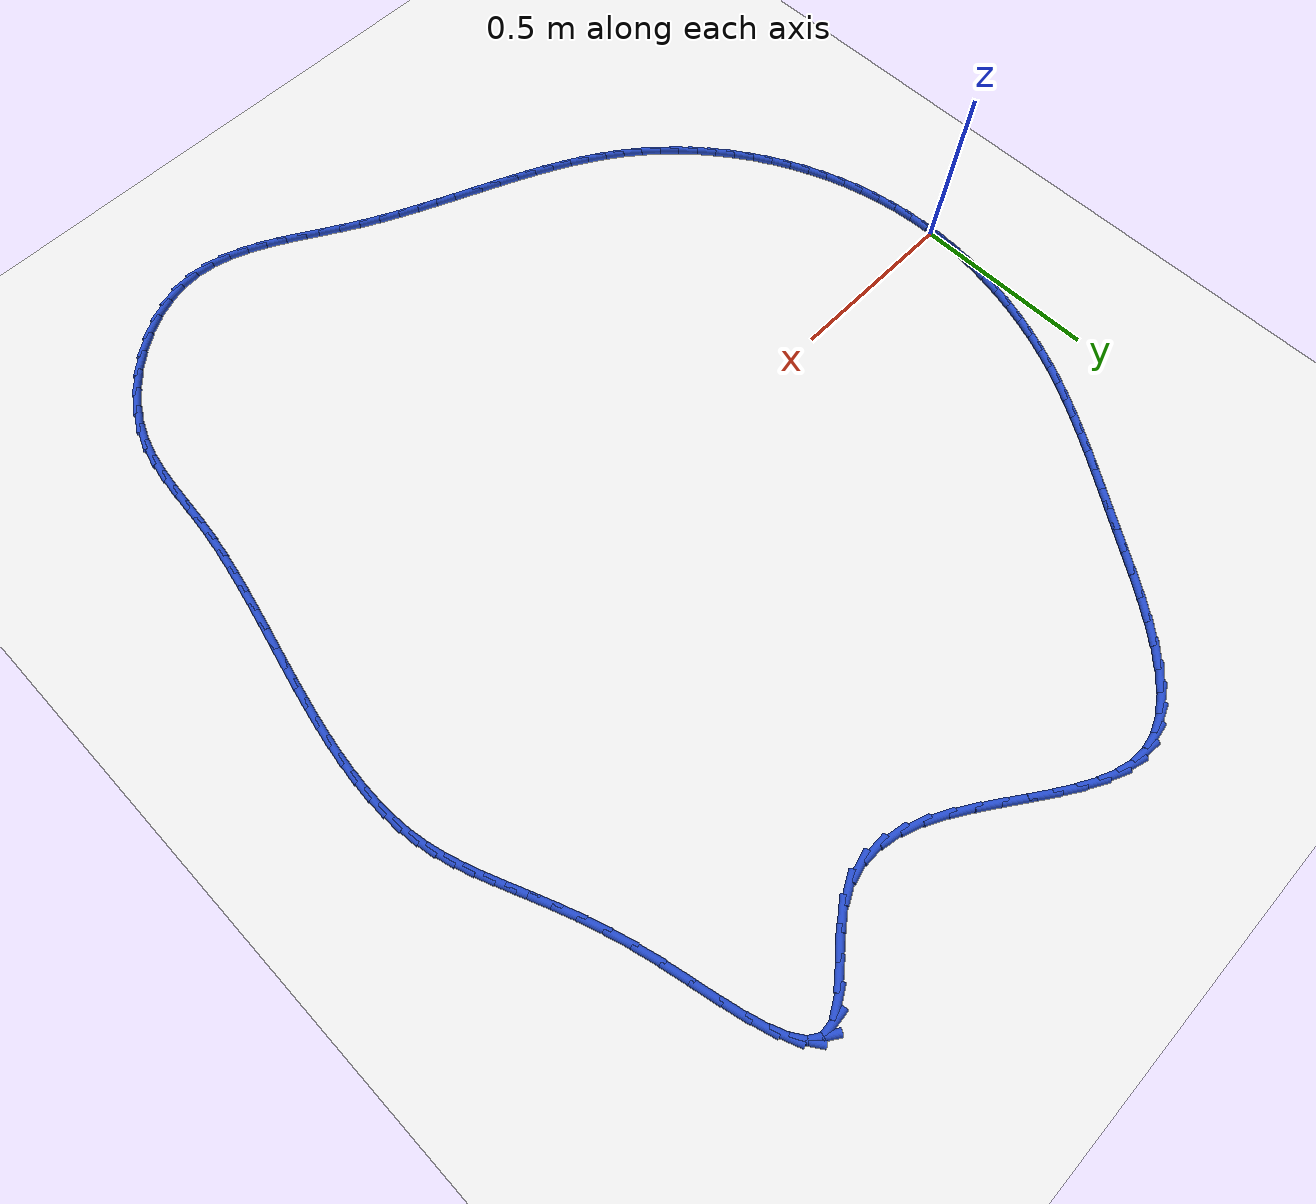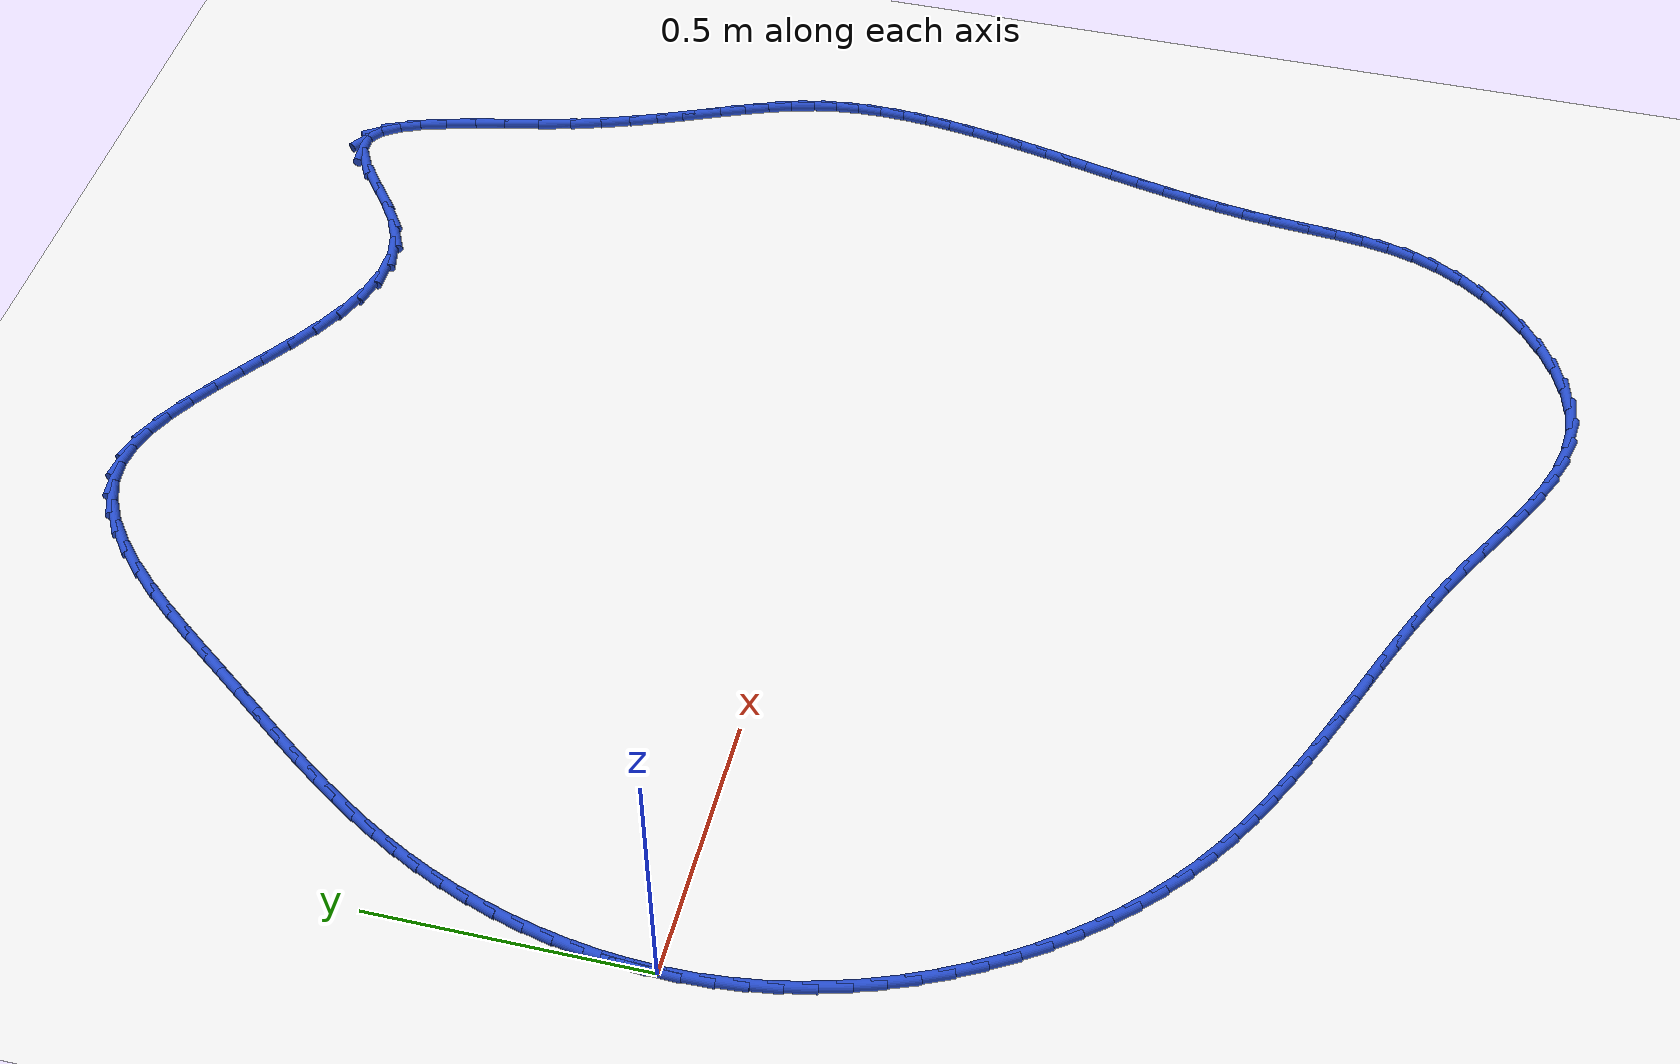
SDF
<sdf version="1.6">
 <world name="default">
  <light name="sun" type="directional">
   <pose>0 0 10 0 -0 0</pose>
   <diffuse>0.8 0.8 0.8 1</diffuse>
   <specular>0.2 0.2 0.2 1</specular>
   <attenuation>
    <range>1000</range>
    <constant>0.9</constant>
    <linear>0.01</linear>
    <quadratic>0.001</quadratic>
   </attenuation>
   <direction>-0.5 0.1 -0.9</direction>
  </light>
  <model name="ground_plane">
   <static>1</static>
   <link name="link">
    <collision name="collision">
     <geometry><plane><normal>0 0 1</normal><size>100 100</size></plane></geometry>
     <surface><friction><ode><mu>100</mu><mu2>50</mu2></ode></friction></surface>
    </collision>
    <visual name="visual">
     <cast_shadows>0</cast_shadows>
     <geometry><plane><normal>0 0 1</normal><size>100 100</size></plane></geometry>
     <material>
      <script><uri>file://media/materials/scripts/gazebo.material</uri><name>Gazebo/WhiteGlow</name></script>
     </material>
    </visual>
   </link>
  </model>
  <gravity>0 0 -9.8</gravity>
  <magnetic_field>6e-06 2.3e-05 -4.2e-05</magnetic_field>
  <atmosphere type="adiabatic"/>
  <physics name="default_physics" default="0" type="ode">
   <max_step_size>0.001</max_step_size>
   <real_time_factor>1</real_time_factor>
   <real_time_update_rate>1000</real_time_update_rate>
  </physics>
  <scene><ambient>0.4 0.4 0.4 1</ambient><background>0.7 0.7 0.7 1</background><shadows>1</shadows></scene>
  <spherical_coordinates>
   <surface_model>EARTH_WGS84</surface_model>
   <latitude_deg>0</latitude_deg>
   <longitude_deg>0</longitude_deg>
   <elevation>0</elevation>
   <heading_deg>0</heading_deg>
  </spherical_coordinates>
  <model name="line">
   <link name="link_0">
    <pose>-3.122502256758253e-17 -8.326672684688674e-17 0.01 0 1.57 1.5301949164621702</pose>
    <collision name="collision">
     <geometry><cylinder><radius>0.01</radius><length>0.08</length></cylinder></geometry>
    </collision>
    <visual name="visual">
     <material>
      <script><name>Gazebo/Blue</name><uri>file://media/materials/scripts/gazebo.material</uri></script>
     </material>
     <geometry><cylinder><radius>0.01</radius><length>0.08</length></cylinder></geometry>
    </visual>
   </link>
   <link name="link_1">
    <pose>0.0022075486330669406 0.054341350520344396 0.01 0 1.57 1.4746755640071965</pose>
    <collision name="collision">
     <geometry><cylinder><radius>0.01</radius><length>0.08</length></cylinder></geometry>
    </collision>
    <visual name="visual">
     <material>
      <script><name>Gazebo/Blue</name><uri>file://media/materials/scripts/gazebo.material</uri></script>
     </material>
     <geometry><cylinder><radius>0.01</radius><length>0.08</length></cylinder></geometry>
    </visual>
   </link>
   <link name="link_2">
    <pose>0.007438938822848464 0.10859881599953379 0.01 0 1.57 1.422006612447328</pose>
    <collision name="collision">
     <geometry><cylinder><radius>0.01</radius><length>0.08</length></cylinder></geometry>
    </collision>
    <visual name="visual">
     <material>
      <script><name>Gazebo/Blue</name><uri>file://media/materials/scripts/gazebo.material</uri></script>
     </material>
     <geometry><cylinder><radius>0.01</radius><length>0.08</length></cylinder></geometry>
    </visual>
   </link>
   <link name="link_3">
    <pose>0.015526090274731199 0.1625500209821812 0.01 0 1.57 1.3717756762877462</pose>
    <collision name="collision">
     <geometry><cylinder><radius>0.01</radius><length>0.08</length></cylinder></geometry>
    </collision>
    <visual name="visual">
     <material>
      <script><name>Gazebo/Blue</name><uri>file://media/materials/scripts/gazebo.material</uri></script>
     </material>
     <geometry><cylinder><radius>0.01</radius><length>0.08</length></cylinder></geometry>
    </visual>
   </link>
   <link name="link_4">
    <pose>0.026300922694101798 0.2159725900128996 0.01 0 1.57 1.3235577637473384</pose>
    <collision name="collision">
     <geometry><cylinder><radius>0.01</radius><length>0.08</length></cylinder></geometry>
    </collision>
    <visual name="visual">
     <material>
      <script><name>Gazebo/Blue</name><uri>file://media/materials/scripts/gazebo.material</uri></script>
     </material>
     <geometry><cylinder><radius>0.01</radius><length>0.08</length></cylinder></geometry>
    </visual>
   </link>
   <link name="link_5">
    <pose>0.03959535578634695 0.2686441476363022 0.01 0 1.57 1.2769189393205005</pose>
    <collision name="collision">
     <geometry><cylinder><radius>0.01</radius><length>0.08</length></cylinder></geometry>
    </collision>
    <visual name="visual">
     <material>
      <script><name>Gazebo/Blue</name><uri>file://media/materials/scripts/gazebo.material</uri></script>
     </material>
     <geometry><cylinder><radius>0.01</radius><length>0.08</length></cylinder></geometry>
    </visual>
   </link>
   <link name="link_6">
    <pose>0.055241309256853305 0.32034231839700195 0.01 0 1.57 1.2314154283046022</pose>
    <collision name="collision">
     <geometry><cylinder><radius>0.01</radius><length>0.08</length></cylinder></geometry>
    </collision>
    <visual name="visual">
     <material>
      <script><name>Gazebo/Blue</name><uri>file://media/materials/scripts/gazebo.material</uri></script>
     </material>
     <geometry><cylinder><radius>0.01</radius><length>0.08</length></cylinder></geometry>
    </visual>
   </link>
   <link name="link_7">
    <pose>0.0730707028110075 0.3708447268396117 0.01 0 1.57 1.1865888610625632</pose>
    <collision name="collision">
     <geometry><cylinder><radius>0.01</radius><length>0.08</length></cylinder></geometry>
    </collision>
    <visual name="visual">
     <material>
      <script><name>Gazebo/Blue</name><uri>file://media/materials/scripts/gazebo.material</uri></script>
     </material>
     <geometry><cylinder><radius>0.01</radius><length>0.08</length></cylinder></geometry>
    </visual>
   </link>
   <link name="link_8">
    <pose>0.09291545615419627 0.4199289975087449 0.01 0 1.57 1.1421388670999895</pose>
    <collision name="collision">
     <geometry><cylinder><radius>0.01</radius><length>0.08</length></cylinder></geometry>
    </collision>
    <visual name="visual">
     <material>
      <script><name>Gazebo/Blue</name><uri>file://media/materials/scripts/gazebo.material</uri></script>
     </material>
     <geometry><cylinder><radius>0.01</radius><length>0.08</length></cylinder></geometry>
    </visual>
   </link>
   <link name="link_9">
    <pose>0.11461238780194348 0.46740617316167077 0.01 0 1.57 1.0997445924066682</pose>
    <collision name="collision">
     <geometry><cylinder><radius>0.01</radius><length>0.08</length></cylinder></geometry>
    </collision>
    <visual name="visual">
     <material>
      <script><name>Gazebo/Blue</name><uri>file://media/materials/scripts/gazebo.material</uri></script>
     </material>
     <geometry><cylinder><radius>0.01</radius><length>0.08</length></cylinder></geometry>
    </visual>
   </link>
   <link name="link_10">
    <pose>0.13804722136117467 0.5134209124131082 0.01 0 1.57 1.0611752489337685</pose>
    <collision name="collision">
     <geometry><cylinder><radius>0.01</radius><length>0.08</length></cylinder></geometry>
    </collision>
    <visual name="visual">
     <material>
      <script><name>Gazebo/Blue</name><uri>file://media/materials/scripts/gazebo.material</uri></script>
     </material>
     <geometry><cylinder><radius>0.01</radius><length>0.08</length></cylinder></geometry>
    </visual>
   </link>
   <link name="link_11">
    <pose>0.16313379013094395 0.5583096297619466 0.01 0 1.57 1.0271878848807843</pose>
    <collision name="collision">
     <geometry><cylinder><radius>0.01</radius><length>0.08</length></cylinder></geometry>
    </collision>
    <visual name="visual">
     <material>
      <script><name>Gazebo/Blue</name><uri>file://media/materials/scripts/gazebo.material</uri></script>
     </material>
     <geometry><cylinder><radius>0.01</radius><length>0.08</length></cylinder></geometry>
    </visual>
   </link>
   <link name="link_12">
    <pose>0.18978626299362236 0.6024110289557577 0.01 0 1.57 0.9983243542576741</pose>
    <collision name="collision">
     <geometry><cylinder><radius>0.01</radius><length>0.08</length></cylinder></geometry>
    </collision>
    <visual name="visual">
     <material>
      <script><name>Gazebo/Blue</name><uri>file://media/materials/scripts/gazebo.material</uri></script>
     </material>
     <geometry><cylinder><radius>0.01</radius><length>0.08</length></cylinder></geometry>
    </visual>
   </link>
   <link name="link_13">
    <pose>0.2179188088315812 0.646063813742114 0.01 0 1.57 0.9749143127374696</pose>
    <collision name="collision">
     <geometry><cylinder><radius>0.01</radius><length>0.08</length></cylinder></geometry>
    </collision>
    <visual name="visual">
     <material>
      <script><name>Gazebo/Blue</name><uri>file://media/materials/scripts/gazebo.material</uri></script>
     </material>
     <geometry><cylinder><radius>0.01</radius><length>0.08</length></cylinder></geometry>
    </visual>
   </link>
   <link name="link_14">
    <pose>0.24744559652719156 0.6896066878685875 0.01 0 1.57 0.9570862462830854</pose>
    <collision name="collision">
     <geometry><cylinder><radius>0.01</radius><length>0.08</length></cylinder></geometry>
    </collision>
    <visual name="visual">
     <material>
      <script><name>Gazebo/Blue</name><uri>file://media/materials/scripts/gazebo.material</uri></script>
     </material>
     <geometry><cylinder><radius>0.01</radius><length>0.08</length></cylinder></geometry>
    </visual>
   </link>
   <link name="link_15">
    <pose>0.27828079496282465 0.7333783550827505 0.01 0 1.57 0.944791988539994</pose>
    <collision name="collision">
     <geometry><cylinder><radius>0.01</radius><length>0.08</length></cylinder></geometry>
    </collision>
    <visual name="visual">
     <material>
      <script><name>Gazebo/Blue</name><uri>file://media/materials/scripts/gazebo.material</uri></script>
     </material>
     <geometry><cylinder><radius>0.01</radius><length>0.08</length></cylinder></geometry>
    </visual>
   </link>
   <link name="link_16">
    <pose>0.3103385730208517 0.7777175191321752 0.01 0 1.57 0.9378377933495353</pose>
    <collision name="collision">
     <geometry><cylinder><radius>0.01</radius><length>0.08</length></cylinder></geometry>
    </collision>
    <visual name="visual">
     <material>
      <script><name>Gazebo/Blue</name><uri>file://media/materials/scripts/gazebo.material</uri></script>
     </material>
     <geometry><cylinder><radius>0.01</radius><length>0.08</length></cylinder></geometry>
    </visual>
   </link>
   <link name="link_17">
    <pose>0.3435330995836438 0.8229628837644336 0.01 0 1.57 0.9359165957944917</pose>
    <collision name="collision">
     <geometry><cylinder><radius>0.01</radius><length>0.08</length></cylinder></geometry>
    </collision>
    <visual name="visual">
     <material>
      <script><name>Gazebo/Blue</name><uri>file://media/materials/scripts/gazebo.material</uri></script>
     </material>
     <geometry><cylinder><radius>0.01</radius><length>0.08</length></cylinder></geometry>
    </visual>
   </link>
   <link name="link_18">
    <pose>0.37777854353357204 0.8694531527270976 0.01 0 1.57 0.9385876809876145</pose>
    <collision name="collision">
     <geometry><cylinder><radius>0.01</radius><length>0.08</length></cylinder></geometry>
    </collision>
    <visual name="visual">
     <material>
      <script><name>Gazebo/Blue</name><uri>file://media/materials/scripts/gazebo.material</uri></script>
     </material>
     <geometry><cylinder><radius>0.01</radius><length>0.08</length></cylinder></geometry>
    </visual>
   </link>
   <link name="link_19">
    <pose>0.41298937666527874 0.9175223545100621 0.01 0 1.57 0.9400298390118881</pose>
    <collision name="collision">
     <geometry><cylinder><radius>0.01</radius><length>0.08</length></cylinder></geometry>
    </collision>
    <visual name="visual">
     <material>
      <script><name>Gazebo/Blue</name><uri>file://media/materials/scripts/gazebo.material</uri></script>
     </material>
     <geometry><cylinder><radius>0.01</radius><length>0.08</length></cylinder></geometry>
    </visual>
   </link>
   <link name="link_20">
    <pose>0.4491135422606998 0.9669879065477065 0.01 0 1.57 0.9302275122954669</pose>
    <collision name="collision">
     <geometry><cylinder><radius>0.01</radius><length>0.08</length></cylinder></geometry>
    </collision>
    <visual name="visual">
     <material>
      <script><name>Gazebo/Blue</name><uri>file://media/materials/scripts/gazebo.material</uri></script>
     </material>
     <geometry><cylinder><radius>0.01</radius><length>0.08</length></cylinder></geometry>
    </visual>
   </link>
   <link name="link_21">
    <pose>0.4861623459393318 1.016689269011883 0.01 0 1.57 0.9079745108533863</pose>
    <collision name="collision">
     <geometry><cylinder><radius>0.01</radius><length>0.08</length></cylinder></geometry>
    </collision>
    <visual name="visual">
     <material>
      <script><name>Gazebo/Blue</name><uri>file://media/materials/scripts/gazebo.material</uri></script>
     </material>
     <geometry><cylinder><radius>0.01</radius><length>0.08</length></cylinder></geometry>
    </visual>
   </link>
   <link name="link_22">
    <pose>0.5241541489011883 1.0653570036897888 0.01 0 1.57 0.8720499910200441</pose>
    <collision name="collision">
     <geometry><cylinder><radius>0.01</radius><length>0.08</length></cylinder></geometry>
    </collision>
    <visual name="visual">
     <material>
      <script><name>Gazebo/Blue</name><uri>file://media/materials/scripts/gazebo.material</uri></script>
     </material>
     <geometry><cylinder><radius>0.01</radius><length>0.08</length></cylinder></geometry>
    </visual>
   </link>
   <link name="link_23">
    <pose>0.5631073123462832 1.1117216723686225 0.01 0 1.57 0.8199480555947248</pose>
    <collision name="collision">
     <geometry><cylinder><radius>0.01</radius><length>0.08</length></cylinder></geometry>
    </collision>
    <visual name="visual">
     <material>
      <script><name>Gazebo/Blue</name><uri>file://media/materials/scripts/gazebo.material</uri></script>
     </material>
     <geometry><cylinder><radius>0.01</radius><length>0.08</length></cylinder></geometry>
    </visual>
   </link>
   <link name="link_24">
    <pose>0.6030401974746302 1.1545138368355818 0.01 0 1.57 0.747628342369547</pose>
    <collision name="collision">
     <geometry><cylinder><radius>0.01</radius><length>0.08</length></cylinder></geometry>
    </collision>
    <visual name="visual">
     <material>
      <script><name>Gazebo/Blue</name><uri>file://media/materials/scripts/gazebo.material</uri></script>
     </material>
     <geometry><cylinder><radius>0.01</radius><length>0.08</length></cylinder></geometry>
    </visual>
   </link>
   <link name="link_25">
    <pose>0.6439711654862428 1.192464058877864 0.01 0 1.57 0.6492476990210018</pose>
    <collision name="collision">
     <geometry><cylinder><radius>0.01</radius><length>0.08</length></cylinder></geometry>
    </collision>
    <visual name="visual">
     <material>
      <script><name>Gazebo/Blue</name><uri>file://media/materials/scripts/gazebo.material</uri></script>
     </material>
     <geometry><cylinder><radius>0.01</radius><length>0.08</length></cylinder></geometry>
    </visual>
   </link>
   <link name="link_26">
    <pose>0.685918577581135 1.2243029002826675 0.01 0 1.57 0.5173334805820249</pose>
    <collision name="collision">
     <geometry><cylinder><radius>0.01</radius><length>0.08</length></cylinder></geometry>
    </collision>
    <visual name="visual">
     <material>
      <script><name>Gazebo/Blue</name><uri>file://media/materials/scripts/gazebo.material</uri></script>
     </material>
     <geometry><cylinder><radius>0.01</radius><length>0.08</length></cylinder></geometry>
    </visual>
   </link>
   <link name="link_27">
    <pose>0.7289007949593205 1.2487609228371903 0.01 0 1.57 0.34465117395034406</pose>
    <collision name="collision">
     <geometry><cylinder><radius>0.01</radius><length>0.08</length></cylinder></geometry>
    </collision>
    <visual name="visual">
     <material>
      <script><name>Gazebo/Blue</name><uri>file://media/materials/scripts/gazebo.material</uri></script>
     </material>
     <geometry><cylinder><radius>0.01</radius><length>0.08</length></cylinder></geometry>
    </visual>
   </link>
   <link name="link_28">
    <pose>0.7729361788208124 1.264568688328629 0.01 0 1.57 0.1298019381787671</pose>
    <collision name="collision">
     <geometry><cylinder><radius>0.01</radius><length>0.08</length></cylinder></geometry>
    </collision>
    <visual name="visual">
     <material>
      <script><name>Gazebo/Blue</name><uri>file://media/materials/scripts/gazebo.material</uri></script>
     </material>
     <geometry><cylinder><radius>0.01</radius><length>0.08</length></cylinder></geometry>
    </visual>
   </link>
   <link name="link_29">
    <pose>0.8180430903656257 1.2704567585441826 0.01 0 1.57 -0.10599912128111598</pose>
    <collision name="collision">
     <geometry><cylinder><radius>0.01</radius><length>0.08</length></cylinder></geometry>
    </collision>
    <visual name="visual">
     <material>
      <script><name>Gazebo/Blue</name><uri>file://media/materials/scripts/gazebo.material</uri></script>
     </material>
     <geometry><cylinder><radius>0.01</radius><length>0.08</length></cylinder></geometry>
    </visual>
   </link>
   <link name="link_30">
    <pose>0.8642249118490284 1.265543109299017 0.01 0 1.57 -0.29926819437853347</pose>
    <collision name="collision">
     <geometry><cylinder><radius>0.01</radius><length>0.08</length></cylinder></geometry>
    </collision>
    <visual name="visual">
     <material>
      <script><name>Gazebo/Blue</name><uri>file://media/materials/scripts/gazebo.material</uri></script>
     </material>
     <geometry><cylinder><radius>0.01</radius><length>0.08</length></cylinder></geometry>
    </visual>
   </link>
   <link name="link_31">
    <pose>0.91140613750861 1.2509860687300087 0.01 0 1.57 -0.43553050890431566</pose>
    <collision name="collision">
     <geometry><cylinder><radius>0.01</radius><length>0.08</length></cylinder></geometry>
    </collision>
    <visual name="visual">
     <material>
      <script><name>Gazebo/Blue</name><uri>file://media/materials/scripts/gazebo.material</uri></script>
     </material>
     <geometry><cylinder><radius>0.01</radius><length>0.08</length></cylinder></geometry>
    </visual>
   </link>
   <link name="link_32">
    <pose>0.9594853838971462 1.2286132629973017 0.01 0 1.57 -0.525775889379785</pose>
    <collision name="collision">
     <geometry><cylinder><radius>0.01</radius><length>0.08</length></cylinder></geometry>
    </collision>
    <visual name="visual">
     <material>
      <script><name>Gazebo/Blue</name><uri>file://media/materials/scripts/gazebo.material</uri></script>
     </material>
     <geometry><cylinder><radius>0.01</radius><length>0.08</length></cylinder></geometry>
    </visual>
   </link>
   <link name="link_33">
    <pose>1.0083612523977028 1.200252710608984 0.01 0 1.57 -0.580604778284598</pose>
    <collision name="collision">
     <geometry><cylinder><radius>0.01</radius><length>0.08</length></cylinder></geometry>
    </collision>
    <visual name="visual">
     <material>
      <script><name>Gazebo/Blue</name><uri>file://media/materials/scripts/gazebo.material</uri></script>
     </material>
     <geometry><cylinder><radius>0.01</radius><length>0.08</length></cylinder></geometry>
    </visual>
   </link>
   <link name="link_34">
    <pose>1.0579323443933457 1.1677324300731422 0.01 0 1.57 -0.6071926233033701</pose>
    <collision name="collision">
     <geometry><cylinder><radius>0.01</radius><length>0.08</length></cylinder></geometry>
    </collision>
    <visual name="visual">
     <material>
      <script><name>Gazebo/Blue</name><uri>file://media/materials/scripts/gazebo.material</uri></script>
     </material>
     <geometry><cylinder><radius>0.01</radius><length>0.08</length></cylinder></geometry>
    </visual>
   </link>
   <link name="link_35">
    <pose>1.1080972612671416 1.1328804398978645 0.01 0 1.57 -0.6093406849988908</pose>
    <collision name="collision">
     <geometry><cylinder><radius>0.01</radius><length>0.08</length></cylinder></geometry>
    </collision>
    <visual name="visual">
     <material>
      <script><name>Gazebo/Blue</name><uri>file://media/materials/scripts/gazebo.material</uri></script>
     </material>
     <geometry><cylinder><radius>0.01</radius><length>0.08</length></cylinder></geometry>
    </visual>
   </link>
   <link name="link_36">
    <pose>1.1587546044021553 1.0975247585912382 0.01 0 1.57 -0.5879904892880937</pose>
    <collision name="collision">
     <geometry><cylinder><radius>0.01</radius><length>0.08</length></cylinder></geometry>
    </collision>
    <visual name="visual">
     <material>
      <script><name>Gazebo/Blue</name><uri>file://media/materials/scripts/gazebo.material</uri></script>
     </material>
     <geometry><cylinder><radius>0.01</radius><length>0.08</length></cylinder></geometry>
    </visual>
   </link>
   <link name="link_37">
    <pose>1.209802975181454 1.0634934046613496 0.01 0 1.57 -0.5415102852055295</pose>
    <collision name="collision">
     <geometry><cylinder><radius>0.01</radius><length>0.08</length></cylinder></geometry>
    </collision>
    <visual name="visual">
     <material>
      <script><name>Gazebo/Blue</name><uri>file://media/materials/scripts/gazebo.material</uri></script>
     </material>
     <geometry><cylinder><radius>0.01</radius><length>0.08</length></cylinder></geometry>
    </visual>
   </link>
   <link name="link_38">
    <pose>1.2611409749881033 1.0326143966162873 0.01 0 1.57 -0.4657496203789692</pose>
    <collision name="collision">
     <geometry><cylinder><radius>0.01</radius><length>0.08</length></cylinder></geometry>
    </collision>
    <visual name="visual">
     <material>
      <script><name>Gazebo/Blue</name><uri>file://media/materials/scripts/gazebo.material</uri></script>
     </material>
     <geometry><cylinder><radius>0.01</radius><length>0.08</length></cylinder></geometry>
    </visual>
   </link>
   <link name="link_39">
    <pose>1.312667205205169 1.0067157529641375 0.01 0 1.57 -0.354267911805755</pose>
    <collision name="collision">
     <geometry><cylinder><radius>0.01</radius><length>0.08</length></cylinder></geometry>
    </collision>
    <visual name="visual">
     <material>
      <script><name>Gazebo/Blue</name><uri>file://media/materials/scripts/gazebo.material</uri></script>
     </material>
     <geometry><cylinder><radius>0.01</radius><length>0.08</length></cylinder></geometry>
    </visual>
   </link>
   <link name="link_40">
    <pose>1.364280267215717 0.9876254922129887 0.01 0 1.57 -0.1998943837817718</pose>
    <collision name="collision">
     <geometry><cylinder><radius>0.01</radius><length>0.08</length></cylinder></geometry>
    </collision>
    <visual name="visual">
     <material>
      <script><name>Gazebo/Blue</name><uri>file://media/materials/scripts/gazebo.material</uri></script>
     </material>
     <geometry><cylinder><radius>0.01</radius><length>0.08</length></cylinder></geometry>
    </visual>
   </link>
   <link name="link_41">
    <pose>1.415878762402814 0.9771716328709275 0.01 0 1.57 0.00020512929372362614</pose>
    <collision name="collision">
     <geometry><cylinder><radius>0.01</radius><length>0.08</length></cylinder></geometry>
    </collision>
    <visual name="visual">
     <material>
      <script><name>Gazebo/Blue</name><uri>file://media/materials/scripts/gazebo.material</uri></script>
     </material>
     <geometry><cylinder><radius>0.01</radius><length>0.08</length></cylinder></geometry>
    </visual>
   </link>
   <link name="link_42">
    <pose>1.4673612921495258 0.9771821934460416 0.01 0 1.57 0.235533162386888</pose>
    <collision name="collision">
     <geometry><cylinder><radius>0.01</radius><length>0.08</length></cylinder></geometry>
    </collision>
    <visual name="visual">
     <material>
      <script><name>Gazebo/Blue</name><uri>file://media/materials/scripts/gazebo.material</uri></script>
     </material>
     <geometry><cylinder><radius>0.01</radius><length>0.08</length></cylinder></geometry>
    </visual>
   </link>
   <link name="link_43">
    <pose>1.5186264578389173 0.9894851924464179 0.01 0 1.57 0.47116439461644616</pose>
    <collision name="collision">
     <geometry><cylinder><radius>0.01</radius><length>0.08</length></cylinder></geometry>
    </collision>
    <visual name="visual">
     <material>
      <script><name>Gazebo/Blue</name><uri>file://media/materials/scripts/gazebo.material</uri></script>
     </material>
     <geometry><cylinder><radius>0.01</radius><length>0.08</length></cylinder></geometry>
    </visual>
   </link>
   <link name="link_44">
    <pose>1.569516032798952 1.015409950415184 0.01 0 1.57 0.6207179666237673</pose>
    <collision name="collision">
     <geometry><cylinder><radius>0.01</radius><length>0.08</length></cylinder></geometry>
    </collision>
    <visual name="visual">
     <material>
      <script><name>Gazebo/Blue</name><uri>file://media/materials/scripts/gazebo.material</uri></script>
     </material>
     <geometry><cylinder><radius>0.01</radius><length>0.08</length></cylinder></geometry>
    </visual>
   </link>
   <link name="link_45">
    <pose>1.6192673910329116 1.0509818458076052 0.01 0 1.57 0.675440867677812</pose>
    <collision name="collision">
     <geometry><cylinder><radius>0.01</radius><length>0.08</length></cylinder></geometry>
    </collision>
    <visual name="visual">
     <material>
      <script><name>Gazebo/Blue</name><uri>file://media/materials/scripts/gazebo.material</uri></script>
     </material>
     <geometry><cylinder><radius>0.01</radius><length>0.08</length></cylinder></geometry>
    </visual>
   </link>
   <link name="link_46">
    <pose>1.666753109490665 1.0890249589203578 0.01 0 1.57 0.6468089882605459</pose>
    <collision name="collision">
     <geometry><cylinder><radius>0.01</radius><length>0.08</length></cylinder></geometry>
    </collision>
    <visual name="visual">
     <material>
      <script><name>Gazebo/Blue</name><uri>file://media/materials/scripts/gazebo.material</uri></script>
     </material>
     <geometry><cylinder><radius>0.01</radius><length>0.08</length></cylinder></geometry>
    </visual>
   </link>
   <link name="link_47">
    <pose>1.7108407209499121 1.1223191046183927 0.01 0 1.57 0.49443216344180696</pose>
    <collision name="collision">
     <geometry><cylinder><radius>0.01</radius><length>0.08</length></cylinder></geometry>
    </collision>
    <visual name="visual">
     <material>
      <script><name>Gazebo/Blue</name><uri>file://media/materials/scripts/gazebo.material</uri></script>
     </material>
     <geometry><cylinder><radius>0.01</radius><length>0.08</length></cylinder></geometry>
    </visual>
   </link>
   <link name="link_48">
    <pose>1.750397758188359 1.1436440977666649 0.01 0 1.57 0.06967872058787611</pose>
    <collision name="collision">
     <geometry><cylinder><radius>0.01</radius><length>0.08</length></cylinder></geometry>
    </collision>
    <visual name="visual">
     <material>
      <script><name>Gazebo/Blue</name><uri>file://media/materials/scripts/gazebo.material</uri></script>
     </material>
     <geometry><cylinder><radius>0.01</radius><length>0.08</length></cylinder></geometry>
    </visual>
   </link>
   <link name="link_49">
    <pose>1.7843390064456652 1.1460129153963379 0.01 0 1.57 -0.5753348081033857</pose>
    <collision name="collision">
     <geometry><cylinder><radius>0.01</radius><length>0.08</length></cylinder></geometry>
    </collision>
    <visual name="visual">
     <material>
      <script><name>Gazebo/Blue</name><uri>file://media/materials/scripts/gazebo.material</uri></script>
     </material>
     <geometry><cylinder><radius>0.01</radius><length>0.08</length></cylinder></geometry>
    </visual>
   </link>
   <link name="link_50">
    <pose>1.8126375712273077 1.1276607015006925 0.01 0 1.57 -0.9851932827144391</pose>
    <collision name="collision">
     <geometry><cylinder><radius>0.01</radius><length>0.08</length></cylinder></geometry>
    </collision>
    <visual name="visual">
     <material>
      <script><name>Gazebo/Blue</name><uri>file://media/materials/scripts/gazebo.material</uri></script>
     </material>
     <geometry><cylinder><radius>0.01</radius><length>0.08</length></cylinder></geometry>
    </visual>
   </link>
   <link name="link_51">
    <pose>1.8363092903695477 1.0919678500545753 0.01 0 1.57 -1.1845361011437634</pose>
    <collision name="collision">
     <geometry><cylinder><radius>0.01</radius><length>0.08</length></cylinder></geometry>
    </collision>
    <visual name="visual">
     <material>
      <script><name>Gazebo/Blue</name><uri>file://media/materials/scripts/gazebo.material</uri></script>
     </material>
     <geometry><cylinder><radius>0.01</radius><length>0.08</length></cylinder></geometry>
    </visual>
   </link>
   <link name="link_52">
    <pose>1.8564141363684141 1.0425325327411221 0.01 0 1.57 -1.2835939373152463</pose>
    <collision name="collision">
     <geometry><cylinder><radius>0.01</radius><length>0.08</length></cylinder></geometry>
    </collision>
    <visual name="visual">
     <material>
      <script><name>Gazebo/Blue</name><uri>file://media/materials/scripts/gazebo.material</uri></script>
     </material>
     <geometry><cylinder><radius>0.01</radius><length>0.08</length></cylinder></geometry>
    </visual>
   </link>
   <link name="link_53">
    <pose>1.8740120817199382 0.982952921243472 0.01 0 1.57 -1.3312394661057148</pose>
    <collision name="collision">
     <geometry><cylinder><radius>0.01</radius><length>0.08</length></cylinder></geometry>
    </collision>
    <visual name="visual">
     <material>
      <script><name>Gazebo/Blue</name><uri>file://media/materials/scripts/gazebo.material</uri></script>
     </material>
     <geometry><cylinder><radius>0.01</radius><length>0.08</length></cylinder></geometry>
    </visual>
   </link>
   <link name="link_54">
    <pose>1.890163098920149 0.9168271872447609 0.01 0 1.57 -1.346418266558759</pose>
    <collision name="collision">
     <geometry><cylinder><radius>0.01</radius><length>0.08</length></cylinder></geometry>
    </collision>
    <visual name="visual">
     <material>
      <script><name>Gazebo/Blue</name><uri>file://media/materials/scripts/gazebo.material</uri></script>
     </material>
     <geometry><cylinder><radius>0.01</radius><length>0.08</length></cylinder></geometry>
    </visual>
   </link>
   <link name="link_55">
    <pose>1.9059271604650778 0.8477535024281256 0.01 0 1.57 -1.3350378959349</pose>
    <collision name="collision">
     <geometry><cylinder><radius>0.01</radius><length>0.08</length></cylinder></geometry>
    </collision>
    <visual name="visual">
     <material>
      <script><name>Gazebo/Blue</name><uri>file://media/materials/scripts/gazebo.material</uri></script>
     </material>
     <geometry><cylinder><radius>0.01</radius><length>0.08</length></cylinder></geometry>
    </visual>
   </link>
   <link name="link_56">
    <pose>1.9223642388507542 0.7793300384767047 0.01 0 1.57 -1.2976901745498084</pose>
    <collision name="collision">
     <geometry><cylinder><radius>0.01</radius><length>0.08</length></cylinder></geometry>
    </collision>
    <visual name="visual">
     <material>
      <script><name>Gazebo/Blue</name><uri>file://media/materials/scripts/gazebo.material</uri></script>
     </material>
     <geometry><cylinder><radius>0.01</radius><length>0.08</length></cylinder></geometry>
    </visual>
   </link>
   <link name="link_57">
    <pose>1.9404218600993848 0.7148627304492015 0.01 0 1.57 -1.2535801301103584</pose>
    <collision name="collision">
     <geometry><cylinder><radius>0.01</radius><length>0.08</length></cylinder></geometry>
    </collision>
    <visual name="visual">
     <material>
      <script><name>Gazebo/Blue</name><uri>file://media/materials/scripts/gazebo.material</uri></script>
     </material>
     <geometry><cylinder><radius>0.01</radius><length>0.08</length></cylinder></geometry>
    </visual>
   </link>
   <link name="link_58">
    <pose>1.9600519550308622 0.6550700656050981 0.01 0 1.57 -1.2163077514050005</pose>
    <collision name="collision">
     <geometry><cylinder><radius>0.01</radius><length>0.08</length></cylinder></geometry>
    </collision>
    <visual name="visual">
     <material>
      <script><name>Gazebo/Blue</name><uri>file://media/materials/scripts/gazebo.material</uri></script>
     </material>
     <geometry><cylinder><radius>0.01</radius><length>0.08</length></cylinder></geometry>
    </visual>
   </link>
   <link name="link_59">
    <pose>1.98068657834252 0.599319427536374 0.01 0 1.57 -1.1882250950180535</pose>
    <collision name="collision">
     <geometry><cylinder><radius>0.01</radius><length>0.08</length></cylinder></geometry>
    </collision>
    <visual name="visual">
     <material>
      <script><name>Gazebo/Blue</name><uri>file://media/materials/scripts/gazebo.material</uri></script>
     </material>
     <geometry><cylinder><radius>0.01</radius><length>0.08</length></cylinder></geometry>
    </visual>
   </link>
   <link name="link_60">
    <pose>2.0017532670872145 0.546966458949531 0.01 0 1.57 -1.171550976726147</pose>
    <collision name="collision">
     <geometry><cylinder><radius>0.01</radius><length>0.08</length></cylinder></geometry>
    </collision>
    <visual name="visual">
     <material>
      <script><name>Gazebo/Blue</name><uri>file://media/materials/scripts/gazebo.material</uri></script>
     </material>
     <geometry><cylinder><radius>0.01</radius><length>0.08</length></cylinder></geometry>
    </visual>
   </link>
   <link name="link_61">
    <pose>2.0226795583178045 0.4973668025510696 0.01 0 1.57 -1.168392835623943</pose>
    <collision name="collision">
     <geometry><cylinder><radius>0.01</radius><length>0.08</length></cylinder></geometry>
    </collision>
    <visual name="visual">
     <material>
      <script><name>Gazebo/Blue</name><uri>file://media/materials/scripts/gazebo.material</uri></script>
     </material>
     <geometry><cylinder><radius>0.01</radius><length>0.08</length></cylinder></geometry>
    </visual>
   </link>
   <link name="link_62">
    <pose>2.0428929890871457 0.44987610104749176 0.01 0 1.57 -1.180631827880012</pose>
    <collision name="collision">
     <geometry><cylinder><radius>0.01</radius><length>0.08</length></cylinder></geometry>
    </collision>
    <visual name="visual">
     <material>
      <script><name>Gazebo/Blue</name><uri>file://media/materials/scripts/gazebo.material</uri></script>
     </material>
     <geometry><cylinder><radius>0.01</radius><length>0.08</length></cylinder></geometry>
    </visual>
   </link>
   <link name="link_63">
    <pose>2.0618210964480967 0.403849997145298 0.01 0 1.57 -1.209736792305382</pose>
    <collision name="collision">
     <geometry><cylinder><radius>0.01</radius><length>0.08</length></cylinder></geometry>
    </collision>
    <visual name="visual">
     <material>
      <script><name>Gazebo/Blue</name><uri>file://media/materials/scripts/gazebo.material</uri></script>
     </material>
     <geometry><cylinder><radius>0.01</radius><length>0.08</length></cylinder></geometry>
    </visual>
   </link>
   <link name="link_64">
    <pose>2.0788914174535145 0.3586441335509904 0.01 0 1.57 -1.2564574136945228</pose>
    <collision name="collision">
     <geometry><cylinder><radius>0.01</radius><length>0.08</length></cylinder></geometry>
    </collision>
    <visual name="visual">
     <material>
      <script><name>Gazebo/Blue</name><uri>file://media/materials/scripts/gazebo.material</uri></script>
     </material>
     <geometry><cylinder><radius>0.01</radius><length>0.08</length></cylinder></geometry>
    </visual>
   </link>
   <link name="link_65">
    <pose>2.093531489156255 0.31361415297106937 0.01 0 1.57 -1.3203899601440998</pose>
    <collision name="collision">
     <geometry><cylinder><radius>0.01</radius><length>0.08</length></cylinder></geometry>
    </collision>
    <visual name="visual">
     <material>
      <script><name>Gazebo/Blue</name><uri>file://media/materials/scripts/gazebo.material</uri></script>
     </material>
     <geometry><cylinder><radius>0.01</radius><length>0.08</length></cylinder></geometry>
    </visual>
   </link>
   <link name="link_66">
    <pose>2.1051688486091784 0.2681156981120362 0.01 0 1.57 -1.398470611467378</pose>
    <collision name="collision">
     <geometry><cylinder><radius>0.01</radius><length>0.08</length></cylinder></geometry>
    </collision>
    <visual name="visual">
     <material>
      <script><name>Gazebo/Blue</name><uri>file://media/materials/scripts/gazebo.material</uri></script>
     </material>
     <geometry><cylinder><radius>0.01</radius><length>0.08</length></cylinder></geometry>
    </visual>
   </link>
   <link name="link_67">
    <pose>2.113275315817419 0.22154073248576012 0.01 0 1.57 -1.4756640407196244</pose>
    <collision name="collision">
     <geometry><cylinder><radius>0.01</radius><length>0.08</length></cylinder></geometry>
    </collision>
    <visual name="visual">
     <material>
      <script><name>Gazebo/Blue</name><uri>file://media/materials/scripts/gazebo.material</uri></script>
     </material>
     <geometry><cylinder><radius>0.01</radius><length>0.08</length></cylinder></geometry>
    </visual>
   </link>
   <link name="link_68">
    <pose>2.1178397856531674 0.1737053235682842 0.01 0 1.57 -1.5433357298941663</pose>
    <collision name="collision">
     <geometry><cylinder><radius>0.01</radius><length>0.08</length></cylinder></geometry>
    </collision>
    <visual name="visual">
     <material>
      <script><name>Gazebo/Blue</name><uri>file://media/materials/scripts/gazebo.material</uri></script>
     </material>
     <geometry><cylinder><radius>0.01</radius><length>0.08</length></cylinder></geometry>
    </visual>
   </link>
   <link name="link_69">
    <pose>2.1191858381598783 0.12470004706826322 0.01 0 1.57 1.5399921952936917</pose>
    <collision name="collision">
     <geometry><cylinder><radius>0.01</radius><length>0.08</length></cylinder></geometry>
    </collision>
    <visual name="visual">
     <material>
      <script><name>Gazebo/Blue</name><uri>file://media/materials/scripts/gazebo.material</uri></script>
     </material>
     <geometry><cylinder><radius>0.01</radius><length>0.08</length></cylinder></geometry>
    </visual>
   </link>
   <link name="link_70">
    <pose>2.1176426805745536 0.07462009410934049 0.01 0 1.57 1.4906081740658474</pose>
    <collision name="collision">
     <geometry><cylinder><radius>0.01</radius><length>0.08</length></cylinder></geometry>
    </collision>
    <visual name="visual">
     <material>
      <script><name>Gazebo/Blue</name><uri>file://media/materials/scripts/gazebo.material</uri></script>
     </material>
     <geometry><cylinder><radius>0.01</radius><length>0.08</length></cylinder></geometry>
    </visual>
   </link>
   <link name="link_71">
    <pose>2.1135395201341995 0.02356065581516082 0.01 0 1.57 1.4494565704134001</pose>
    <collision name="collision">
     <geometry><cylinder><radius>0.01</radius><length>0.08</length></cylinder></geometry>
    </collision>
    <visual name="visual">
     <material>
      <script><name>Gazebo/Blue</name><uri>file://media/materials/scripts/gazebo.material</uri></script>
     </material>
     <geometry><cylinder><radius>0.01</radius><length>0.08</length></cylinder></geometry>
    </visual>
   </link>
   <link name="link_72">
    <pose>2.107205564075819 -0.02838307669063197 0.01 0 1.57 1.4158729123155471</pose>
    <collision name="collision">
     <geometry><cylinder><radius>0.01</radius><length>0.08</length></cylinder></geometry>
    </collision>
    <visual name="visual">
     <material>
      <script><name>Gazebo/Blue</name><uri>file://media/materials/scripts/gazebo.material</uri></script>
     </material>
     <geometry><cylinder><radius>0.01</radius><length>0.08</length></cylinder></geometry>
    </visual>
   </link>
   <link name="link_73">
    <pose>2.0989700196364165 -0.08111591228439458 0.01 0 1.57 1.3892407552816333</pose>
    <collision name="collision">
     <geometry><cylinder><radius>0.01</radius><length>0.08</length></cylinder></geometry>
    </collision>
    <visual name="visual">
     <material>
      <script><name>Gazebo/Blue</name><uri>file://media/materials/scripts/gazebo.material</uri></script>
     </material>
     <geometry><cylinder><radius>0.01</radius><length>0.08</length></cylinder></geometry>
    </visual>
   </link>
   <link name="link_74">
    <pose>2.0891620940529974 -0.13454265984248137 0.01 0 1.57 1.369026245197287</pose>
    <collision name="collision">
     <geometry><cylinder><radius>0.01</radius><length>0.08</length></cylinder></geometry>
    </collision>
    <visual name="visual">
     <material>
      <script><name>Gazebo/Blue</name><uri>file://media/materials/scripts/gazebo.material</uri></script>
     </material>
     <geometry><cylinder><radius>0.01</radius><length>0.08</length></cylinder></geometry>
    </visual>
   </link>
   <link name="link_75">
    <pose>2.0781109945625635 -0.18856812824124902 0.01 0 1.57 1.354793829775612</pose>
    <collision name="collision">
     <geometry><cylinder><radius>0.01</radius><length>0.08</length></cylinder></geometry>
    </collision>
    <visual name="visual">
     <material>
      <script><name>Gazebo/Blue</name><uri>file://media/materials/scripts/gazebo.material</uri></script>
     </material>
     <geometry><cylinder><radius>0.01</radius><length>0.08</length></cylinder></geometry>
    </visual>
   </link>
   <link name="link_76">
    <pose>2.0661459284021215 -0.24309712635705338 0.01 0 1.57 1.3462110961139544</pose>
    <collision name="collision">
     <geometry><cylinder><radius>0.01</radius><length>0.08</length></cylinder></geometry>
    </collision>
    <visual name="visual">
     <material>
      <script><name>Gazebo/Blue</name><uri>file://media/materials/scripts/gazebo.material</uri></script>
     </material>
     <geometry><cylinder><radius>0.01</radius><length>0.08</length></cylinder></geometry>
    </visual>
   </link>
   <link name="link_77">
    <pose>2.053596102808674 -0.29803446306625037 0.01 0 1.57 1.3430479813313254</pose>
    <collision name="collision">
     <geometry><cylinder><radius>0.01</radius><length>0.08</length></cylinder></geometry>
    </collision>
    <visual name="visual">
     <material>
      <script><name>Gazebo/Blue</name><uri>file://media/materials/scripts/gazebo.material</uri></script>
     </material>
     <geometry><cylinder><radius>0.01</radius><length>0.08</length></cylinder></geometry>
    </visual>
   </link>
   <link name="link_78">
    <pose>2.0407907250192263 -0.3532849472451966 0.01 0 1.57 1.3451734871662269</pose>
    <collision name="collision">
     <geometry><cylinder><radius>0.01</radius><length>0.08</length></cylinder></geometry>
    </collision>
    <visual name="visual">
     <material>
      <script><name>Gazebo/Blue</name><uri>file://media/materials/scripts/gazebo.material</uri></script>
     </material>
     <geometry><cylinder><radius>0.01</radius><length>0.08</length></cylinder></geometry>
    </visual>
   </link>
   <link name="link_79">
    <pose>2.0280590022707825 -0.40875338777024656 0.01 0 1.57 1.3525515263229446</pose>
    <collision name="collision">
     <geometry><cylinder><radius>0.01</radius><length>0.08</length></cylinder></geometry>
    </collision>
    <visual name="visual">
     <material>
      <script><name>Gazebo/Blue</name><uri>file://media/materials/scripts/gazebo.material</uri></script>
     </material>
     <geometry><cylinder><radius>0.01</radius><length>0.08</length></cylinder></geometry>
    </visual>
   </link>
   <link name="link_80">
    <pose>2.015730141800346 -0.4643445935177567 0.01 0 1.57 1.36523646460539</pose>
    <collision name="collision">
     <geometry><cylinder><radius>0.01</radius><length>0.08</length></cylinder></geometry>
    </collision>
    <visual name="visual">
     <material>
      <script><name>Gazebo/Blue</name><uri>file://media/materials/scripts/gazebo.material</uri></script>
     </material>
     <geometry><cylinder><radius>0.01</radius><length>0.08</length></cylinder></geometry>
    </visual>
   </link>
   <link name="link_81">
    <pose>2.0041333508449215 -0.5199633733640829 0.01 0 1.57 1.3833681033161593</pose>
    <collision name="collision">
     <geometry><cylinder><radius>0.01</radius><length>0.08</length></cylinder></geometry>
    </collision>
    <visual name="visual">
     <material>
      <script><name>Gazebo/Blue</name><uri>file://media/materials/scripts/gazebo.material</uri></script>
     </material>
     <geometry><cylinder><radius>0.01</radius><length>0.08</length></cylinder></geometry>
    </visual>
   </link>
   <link name="link_82">
    <pose>1.9935978366415132 -0.5755145361855822 0.01 0 1.57 1.4071651038024962</pose>
    <collision name="collision">
     <geometry><cylinder><radius>0.01</radius><length>0.08</length></cylinder></geometry>
    </collision>
    <visual name="visual">
     <material>
      <script><name>Gazebo/Blue</name><uri>file://media/materials/scripts/gazebo.material</uri></script>
     </material>
     <geometry><cylinder><radius>0.01</radius><length>0.08</length></cylinder></geometry>
    </visual>
   </link>
   <link name="link_83">
    <pose>1.9844528064271252 -0.6309028908586085 0.01 0 1.57 1.4369150660905905</pose>
    <collision name="collision">
     <geometry><cylinder><radius>0.01</radius><length>0.08</length></cylinder></geometry>
    </collision>
    <visual name="visual">
     <material>
      <script><name>Gazebo/Blue</name><uri>file://media/materials/scripts/gazebo.material</uri></script>
     </material>
     <geometry><cylinder><radius>0.01</radius><length>0.08</length></cylinder></geometry>
    </visual>
   </link>
   <link name="link_84">
    <pose>1.9770274674387625 -0.6860332462595187 0.01 0 1.57 1.4710698186680982</pose>
    <collision name="collision">
     <geometry><cylinder><radius>0.01</radius><length>0.08</length></cylinder></geometry>
    </collision>
    <visual name="visual">
     <material>
      <script><name>Gazebo/Blue</name><uri>file://media/materials/scripts/gazebo.material</uri></script>
     </material>
     <geometry><cylinder><radius>0.01</radius><length>0.08</length></cylinder></geometry>
    </visual>
   </link>
   <link name="link_85">
    <pose>1.971546652787522 -0.7408093845928616 0.01 0 1.57 1.4900256893813428</pose>
    <collision name="collision">
     <geometry><cylinder><radius>0.01</radius><length>0.08</length></cylinder></geometry>
    </collision>
    <visual name="visual">
     <material>
      <script><name>Gazebo/Blue</name><uri>file://media/materials/scripts/gazebo.material</uri></script>
     </material>
     <geometry><cylinder><radius>0.01</radius><length>0.08</length></cylinder></geometry>
    </visual>
   </link>
   <link name="link_86">
    <pose>1.9671500280511152 -0.795124413857269 0.01 0 1.57 1.481411118621205</pose>
    <collision name="collision">
     <geometry><cylinder><radius>0.01</radius><length>0.08</length></cylinder></geometry>
    </collision>
    <visual name="visual">
     <material>
      <script><name>Gazebo/Blue</name><uri>file://media/materials/scripts/gazebo.material</uri></script>
     </material>
     <geometry><cylinder><radius>0.01</radius><length>0.08</length></cylinder></geometry>
    </visual>
   </link>
   <link name="link_87">
    <pose>1.962333570487084 -0.8488651104376221 0.01 0 1.57 1.4442679698666003</pose>
    <collision name="collision">
     <geometry><cylinder><radius>0.01</radius><length>0.08</length></cylinder></geometry>
    </collision>
    <visual name="visual">
     <material>
      <script><name>Gazebo/Blue</name><uri>file://media/materials/scripts/gazebo.material</uri></script>
     </material>
     <geometry><cylinder><radius>0.01</radius><length>0.08</length></cylinder></geometry>
    </visual>
   </link>
   <link name="link_88">
    <pose>1.9555848012061297 -0.9019181675402597 0.01 0 1.57 1.3781319599760538</pose>
    <collision name="collision">
     <geometry><cylinder><radius>0.01</radius><length>0.08</length></cylinder></geometry>
    </collision>
    <visual name="visual">
     <material>
      <script><name>Gazebo/Blue</name><uri>file://media/materials/scripts/gazebo.material</uri></script>
     </material>
     <geometry><cylinder><radius>0.01</radius><length>0.08</length></cylinder></geometry>
    </visual>
   </link>
   <link name="link_89">
    <pose>1.9453912413189531 -0.9541702783715214 0.01 0 1.57 1.2838225735105437</pose>
    <collision name="collision">
     <geometry><cylinder><radius>0.01</radius><length>0.08</length></cylinder></geometry>
    </collision>
    <visual name="visual">
     <material>
      <script><name>Gazebo/Blue</name><uri>file://media/materials/scripts/gazebo.material</uri></script>
     </material>
     <geometry><cylinder><radius>0.01</radius><length>0.08</length></cylinder></geometry>
    </visual>
   </link>
   <link name="link_90">
    <pose>1.9302404119362537 -1.005508136137747 0.01 0 1.57 1.165534682171573</pose>
    <collision name="collision">
     <geometry><cylinder><radius>0.01</radius><length>0.08</length></cylinder></geometry>
    </collision>
    <visual name="visual">
     <material>
      <script><name>Gazebo/Blue</name><uri>file://media/materials/scripts/gazebo.material</uri></script>
     </material>
     <geometry><cylinder><radius>0.01</radius><length>0.08</length></cylinder></geometry>
    </visual>
   </link>
   <link name="link_91">
    <pose>1.908663253457374 -1.0558034537614167 0.01 0 1.57 1.043882975995537</pose>
    <collision name="collision">
     <geometry><cylinder><radius>0.01</radius><length>0.08</length></cylinder></geometry>
    </collision>
    <visual name="visual">
     <material>
      <script><name>Gazebo/Blue</name><uri>file://media/materials/scripts/gazebo.material</uri></script>
     </material>
     <geometry><cylinder><radius>0.01</radius><length>0.08</length></cylinder></geometry>
    </visual>
   </link>
   <link name="link_92">
    <pose>1.8803079518883061 -1.1045424782384246 0.01 0 1.57 0.9328051296785308</pose>
    <collision name="collision">
     <geometry><cylinder><radius>0.01</radius><length>0.08</length></cylinder></geometry>
    </collision>
    <visual name="visual">
     <material>
      <script><name>Gazebo/Blue</name><uri>file://media/materials/scripts/gazebo.material</uri></script>
     </material>
     <geometry><cylinder><radius>0.01</radius><length>0.08</length></cylinder></geometry>
    </visual>
   </link>
   <link name="link_93">
    <pose>1.8460100931145427 -1.1508017863971947 0.01 0 1.57 0.8278260931363953</pose>
    <collision name="collision">
     <geometry><cylinder><radius>0.01</radius><length>0.08</length></cylinder></geometry>
    </collision>
    <visual name="visual">
     <material>
      <script><name>Gazebo/Blue</name><uri>file://media/materials/scripts/gazebo.material</uri></script>
     </material>
     <geometry><cylinder><radius>0.01</radius><length>0.08</length></cylinder></geometry>
    </visual>
   </link>
   <link name="link_94">
    <pose>1.8066627294794135 -1.1936381283053334 0.01 0 1.57 0.7240691879717912</pose>
    <collision name="collision">
     <geometry><cylinder><radius>0.01</radius><length>0.08</length></cylinder></geometry>
    </collision>
    <visual name="visual">
     <material>
      <script><name>Gazebo/Blue</name><uri>file://media/materials/scripts/gazebo.material</uri></script>
     </material>
     <geometry><cylinder><radius>0.01</radius><length>0.08</length></cylinder></geometry>
    </visual>
   </link>
   <link name="link_95">
    <pose>1.7631589133262495 -1.2321082540304489 0.01 0 1.57 0.6167791932416632</pose>
    <collision name="collision">
     <geometry><cylinder><radius>0.01</radius><length>0.08</length></cylinder></geometry>
    </collision>
    <visual name="visual">
     <material>
      <script><name>Gazebo/Blue</name><uri>file://media/materials/scripts/gazebo.material</uri></script>
     </material>
     <geometry><cylinder><radius>0.01</radius><length>0.08</length></cylinder></geometry>
    </visual>
   </link>
   <link name="link_96">
    <pose>1.716391696998383 -1.265268913640145 0.01 0 1.57 0.5010020748747912</pose>
    <collision name="collision">
     <geometry><cylinder><radius>0.01</radius><length>0.08</length></cylinder></geometry>
    </collision>
    <visual name="visual">
     <material>
      <script><name>Gazebo/Blue</name><uri>file://media/materials/scripts/gazebo.material</uri></script>
     </material>
     <geometry><cylinder><radius>0.01</radius><length>0.08</length></cylinder></geometry>
    </visual>
   </link>
   <link name="link_97">
    <pose>1.6672541328391428 -1.292176857202029 0.01 0 1.57 0.3713789474148197</pose>
    <collision name="collision">
     <geometry><cylinder><radius>0.01</radius><length>0.08</length></cylinder></geometry>
    </collision>
    <visual name="visual">
     <material>
      <script><name>Gazebo/Blue</name><uri>file://media/materials/scripts/gazebo.material</uri></script>
     </material>
     <geometry><cylinder><radius>0.01</radius><length>0.08</length></cylinder></geometry>
    </visual>
   </link>
   <link name="link_98">
    <pose>1.616639273191861 -1.3118888347837083 0.01 0 1.57 0.22229884004313868</pose>
    <collision name="collision">
     <geometry><cylinder><radius>0.01</radius><length>0.08</length></cylinder></geometry>
    </collision>
    <visual name="visual">
     <material>
      <script><name>Gazebo/Blue</name><uri>file://media/materials/scripts/gazebo.material</uri></script>
     </material>
     <geometry><cylinder><radius>0.01</radius><length>0.08</length></cylinder></geometry>
    </visual>
   </link>
   <link name="link_99">
    <pose>1.565440170399868 -1.323461596452788 0.01 0 1.57 0.05074404058570359</pose>
    <collision name="collision">
     <geometry><cylinder><radius>0.01</radius><length>0.08</length></cylinder></geometry>
    </collision>
    <visual name="visual">
     <material>
      <script><name>Gazebo/Blue</name><uri>file://media/materials/scripts/gazebo.material</uri></script>
     </material>
     <geometry><cylinder><radius>0.01</radius><length>0.08</length></cylinder></geometry>
    </visual>
   </link>
   <link name="link_100">
    <pose>1.5145071946450526 -1.3260483620935375 0.01 0 1.57 -0.11802207664955838</pose>
    <collision name="collision">
     <geometry><cylinder><radius>0.01</radius><length>0.08</length></cylinder></geometry>
    </collision>
    <visual name="visual">
     <material>
      <script><name>Gazebo/Blue</name><uri>file://media/materials/scripts/gazebo.material</uri></script>
     </material>
     <geometry><cylinder><radius>0.01</radius><length>0.08</length></cylinder></geometry>
    </visual>
   </link>
   <link name="link_101">
    <pose>1.4641277704716773 -1.3200747159836868 0.01 0 1.57 -0.25860944849690926</pose>
    <collision name="collision">
     <geometry><cylinder><radius>0.01</radius><length>0.08</length></cylinder></geometry>
    </collision>
    <visual name="visual">
     <material>
      <script><name>Gazebo/Blue</name><uri>file://media/materials/scripts/gazebo.material</uri></script>
     </material>
     <geometry><cylinder><radius>0.01</radius><length>0.08</length></cylinder></geometry>
    </visual>
   </link>
   <link name="link_102">
    <pose>1.414191689731415 -1.3068649680432003 0.01 0 1.57 -0.3675489950820821</pose>
    <collision name="collision">
     <geometry><cylinder><radius>0.01</radius><length>0.08</length></cylinder></geometry>
    </collision>
    <visual name="visual">
     <material>
      <script><name>Gazebo/Blue</name><uri>file://media/materials/scripts/gazebo.material</uri></script>
     </material>
     <geometry><cylinder><radius>0.01</radius><length>0.08</length></cylinder></geometry>
    </visual>
   </link>
   <link name="link_103">
    <pose>1.3645803824934783 -1.2877623274134962 0.01 0 1.57 -0.44649747052386196</pose>
    <collision name="collision">
     <geometry><cylinder><radius>0.01</radius><length>0.08</length></cylinder></geometry>
    </collision>
    <visual name="visual">
     <material>
      <script><name>Gazebo/Blue</name><uri>file://media/materials/scripts/gazebo.material</uri></script>
     </material>
     <geometry><cylinder><radius>0.01</radius><length>0.08</length></cylinder></geometry>
    </visual>
   </link>
   <link name="link_104">
    <pose>1.3151752788270783 -1.264110003235992 0.01 0 1.57 -0.498695774552913</pose>
    <collision name="collision">
     <geometry><cylinder><radius>0.01</radius><length>0.08</length></cylinder></geometry>
    </collision>
    <visual name="visual">
     <material>
      <script><name>Gazebo/Blue</name><uri>file://media/materials/scripts/gazebo.material</uri></script>
     </material>
     <geometry><cylinder><radius>0.01</radius><length>0.08</length></cylinder></geometry>
    </visual>
   </link>
   <link name="link_105">
    <pose>1.2658578088014278 -1.2372512046521054 0.01 0 1.57 -0.5270985995758147</pose>
    <collision name="collision">
     <geometry><cylinder><radius>0.01</radius><length>0.08</length></cylinder></geometry>
    </collision>
    <visual name="visual">
     <material>
      <script><name>Gazebo/Blue</name><uri>file://media/materials/scripts/gazebo.material</uri></script>
     </material>
     <geometry><cylinder><radius>0.01</radius><length>0.08</length></cylinder></geometry>
    </visual>
   </link>
   <link name="link_106">
    <pose>1.2165094024857388 -1.2085291408032544 0.01 0 1.57 -0.5336086589875081</pose>
    <collision name="collision">
     <geometry><cylinder><radius>0.01</radius><length>0.08</length></cylinder></geometry>
    </collision>
    <visual name="visual">
     <material>
      <script><name>Gazebo/Blue</name><uri>file://media/materials/scripts/gazebo.material</uri></script>
     </material>
     <geometry><cylinder><radius>0.01</radius><length>0.08</length></cylinder></geometry>
    </visual>
   </link>
   <link name="link_107">
    <pose>1.1670114899492219 -1.179287020830856 0.01 0 1.57 -0.5188627123903289</pose>
    <collision name="collision">
     <geometry><cylinder><radius>0.01</radius><length>0.08</length></cylinder></geometry>
    </collision>
    <visual name="visual">
     <material>
      <script><name>Gazebo/Blue</name><uri>file://media/materials/scripts/gazebo.material</uri></script>
     </material>
     <geometry><cylinder><radius>0.01</radius><length>0.08</length></cylinder></geometry>
    </visual>
   </link>
   <link name="link_108">
    <pose>1.1172455059069855 -1.150868021720674 0.01 0 1.57 -0.48758885937392554</pose>
    <collision name="collision">
     <geometry><cylinder><radius>0.01</radius><length>0.08</length></cylinder></geometry>
    </collision>
    <visual name="visual">
     <material>
      <script><name>Gazebo/Blue</name><uri>file://media/materials/scripts/gazebo.material</uri></script>
     </material>
     <geometry><cylinder><radius>0.01</radius><length>0.08</length></cylinder></geometry>
    </visual>
   </link>
   <link name="link_109">
    <pose>1.0671389131670959 -1.1242967460488391 0.01 0 1.57 -0.45758810967995645</pose>
    <collision name="collision">
     <geometry><cylinder><radius>0.01</radius><length>0.08</length></cylinder></geometry>
    </collision>
    <visual name="visual">
     <material>
      <script><name>Gazebo/Blue</name><uri>file://media/materials/scripts/gazebo.material</uri></script>
     </material>
     <geometry><cylinder><radius>0.01</radius><length>0.08</length></cylinder></geometry>
    </visual>
   </link>
   <link name="link_110">
    <pose>1.0167782593615577 -1.0994967220126102 0.01 0 1.57 -0.43302990312347556</pose>
    <collision name="collision">
     <geometry><cylinder><radius>0.01</radius><length>0.08</length></cylinder></geometry>
    </collision>
    <visual name="visual">
     <material>
      <script><name>Gazebo/Blue</name><uri>file://media/materials/scripts/gazebo.material</uri></script>
     </material>
     <geometry><cylinder><radius>0.01</radius><length>0.08</length></cylinder></geometry>
    </visual>
   </link>
   <link name="link_111">
    <pose>0.9662844372383633 -1.076153764831224 0.01 0 1.57 -0.4141317903452567</pose>
    <collision name="collision">
     <geometry><cylinder><radius>0.01</radius><length>0.08</length></cylinder></geometry>
    </collision>
    <visual name="visual">
     <material>
      <script><name>Gazebo/Blue</name><uri>file://media/materials/scripts/gazebo.material</uri></script>
     </material>
     <geometry><cylinder><radius>0.01</radius><length>0.08</length></cylinder></geometry>
    </visual>
   </link>
   <link name="link_112">
    <pose>0.9157783395455056 -1.0539536897239188 0.01 0 1.57 -0.4010711998637591</pose>
    <collision name="collision">
     <geometry><cylinder><radius>0.01</radius><length>0.08</length></cylinder></geometry>
    </collision>
    <visual name="visual">
     <material>
      <script><name>Gazebo/Blue</name><uri>file://media/materials/scripts/gazebo.material</uri></script>
     </material>
     <geometry><cylinder><radius>0.01</radius><length>0.08</length></cylinder></geometry>
    </visual>
   </link>
   <link name="link_113">
    <pose>0.8653808590309766 -1.03258231190993 0.01 0 1.57 -0.3940018386167567</pose>
    <collision name="collision">
     <geometry><cylinder><radius>0.01</radius><length>0.08</length></cylinder></geometry>
    </collision>
    <visual name="visual">
     <material>
      <script><name>Gazebo/Blue</name><uri>file://media/materials/scripts/gazebo.material</uri></script>
     </material>
     <geometry><cylinder><radius>0.01</radius><length>0.08</length></cylinder></geometry>
    </visual>
   </link>
   <link name="link_114">
    <pose>0.8152128884427713 -1.0117254466084964 0.01 0 1.57 -0.393066117928497</pose>
    <collision name="collision">
     <geometry><cylinder><radius>0.01</radius><length>0.08</length></cylinder></geometry>
    </collision>
    <visual name="visual">
     <material>
      <script><name>Gazebo/Blue</name><uri>file://media/materials/scripts/gazebo.material</uri></script>
     </material>
     <geometry><cylinder><radius>0.01</radius><length>0.08</length></cylinder></geometry>
    </visual>
   </link>
   <link name="link_115">
    <pose>0.765395320528881 -0.991068909038854 0.01 0 1.57 -0.3984022344774185</pose>
    <collision name="collision">
     <geometry><cylinder><radius>0.01</radius><length>0.08</length></cylinder></geometry>
    </collision>
    <visual name="visual">
     <material>
      <script><name>Gazebo/Blue</name><uri>file://media/materials/scripts/gazebo.material</uri></script>
     </material>
     <geometry><cylinder><radius>0.01</radius><length>0.08</length></cylinder></geometry>
    </visual>
   </link>
   <link name="link_116">
    <pose>0.716049048037299 -0.9702985144202403 0.01 0 1.57 -0.410144736931504</pose>
    <collision name="collision">
     <geometry><cylinder><radius>0.01</radius><length>0.08</length></cylinder></geometry>
    </collision>
    <visual name="visual">
     <material>
      <script><name>Gazebo/Blue</name><uri>file://media/materials/scripts/gazebo.material</uri></script>
     </material>
     <geometry><cylinder><radius>0.01</radius><length>0.08</length></cylinder></geometry>
    </visual>
   </link>
   <link name="link_117">
    <pose>0.6672949637160176 -0.9491000779718922 0.01 0 1.57 -0.42841746040914097</pose>
    <collision name="collision">
     <geometry><cylinder><radius>0.01</radius><length>0.08</length></cylinder></geometry>
    </collision>
    <visual name="visual">
     <material>
      <script><name>Gazebo/Blue</name><uri>file://media/materials/scripts/gazebo.material</uri></script>
     </material>
     <geometry><cylinder><radius>0.01</radius><length>0.08</length></cylinder></geometry>
    </visual>
   </link>
   <link name="link_118">
    <pose>0.6192539603130314 -0.9271594149130474 0.01 0 1.57 -0.453317773530333</pose>
    <collision name="collision">
     <geometry><cylinder><radius>0.01</radius><length>0.08</length></cylinder></geometry>
    </collision>
    <visual name="visual">
     <material>
      <script><name>Gazebo/Blue</name><uri>file://media/materials/scripts/gazebo.material</uri></script>
     </material>
     <geometry><cylinder><radius>0.01</radius><length>0.08</length></cylinder></geometry>
    </visual>
   </link>
   <link name="link_119">
    <pose>0.5720469305763322 -0.9041623404629432 0.01 0 1.57 -0.48489140064477615</pose>
    <collision name="collision">
     <geometry><cylinder><radius>0.01</radius><length>0.08</length></cylinder></geometry>
    </collision>
    <visual name="visual">
     <material>
      <script><name>Gazebo/Blue</name><uri>file://media/materials/scripts/gazebo.material</uri></script>
     </material>
     <geometry><cylinder><radius>0.01</radius><length>0.08</length></cylinder></geometry>
    </visual>
   </link>
   <link name="link_120">
    <pose>0.5257947672539126 -0.8797946698408156 0.01 0 1.57 -0.5230979680562517</pose>
    <collision name="collision">
     <geometry><cylinder><radius>0.01</radius><length>0.08</length></cylinder></geometry>
    </collision>
    <visual name="visual">
     <material>
      <script><name>Gazebo/Blue</name><uri>file://media/materials/scripts/gazebo.material</uri></script>
     </material>
     <geometry><cylinder><radius>0.01</radius><length>0.08</length></cylinder></geometry>
    </visual>
   </link>
   <link name="link_121">
    <pose>0.48061836309376627 -0.8537422182659027 0.01 0 1.57 -0.5677691906247672</pose>
    <collision name="collision">
     <geometry><cylinder><radius>0.01</radius><length>0.08</length></cylinder></geometry>
    </collision>
    <visual name="visual">
     <material>
      <script><name>Gazebo/Blue</name><uri>file://media/materials/scripts/gazebo.material</uri></script>
     </material>
     <geometry><cylinder><radius>0.01</radius><length>0.08</length></cylinder></geometry>
    </visual>
   </link>
   <link name="link_122">
    <pose>0.43663861084388494 -0.8256908009574407 0.01 0 1.57 -0.6185643966120854</pose>
    <collision name="collision">
     <geometry><cylinder><radius>0.01</radius><length>0.08</length></cylinder></geometry>
    </collision>
    <visual name="visual">
     <material>
      <script><name>Gazebo/Blue</name><uri>file://media/materials/scripts/gazebo.material</uri></script>
     </material>
     <geometry><cylinder><radius>0.01</radius><length>0.08</length></cylinder></geometry>
    </visual>
   </link>
   <link name="link_123">
    <pose>0.39397640325226324 -0.795326233134668 0.01 0 1.57 -0.6746970773772996</pose>
    <collision name="collision">
     <geometry><cylinder><radius>0.01</radius><length>0.08</length></cylinder></geometry>
    </collision>
    <visual name="visual">
     <material>
      <script><name>Gazebo/Blue</name><uri>file://media/materials/scripts/gazebo.material</uri></script>
     </material>
     <geometry><cylinder><radius>0.01</radius><length>0.08</length></cylinder></geometry>
    </visual>
   </link>
   <link name="link_124">
    <pose>0.3527535500572927 -0.7623509159785847 0.01 0 1.57 -0.7318852647772527</pose>
    <collision name="collision">
     <geometry><cylinder><radius>0.01</radius><length>0.08</length></cylinder></geometry>
    </collision>
    <visual name="visual">
     <material>
      <script><name>Gazebo/Blue</name><uri>file://media/materials/scripts/gazebo.material</uri></script>
     </material>
     <geometry><cylinder><radius>0.01</radius><length>0.08</length></cylinder></geometry>
    </visual>
   </link>
   <link name="link_125">
    <pose>0.3131066867079045 -0.7267354090589861 0.01 0 1.57 -0.787316210090194</pose>
    <collision name="collision">
     <geometry><cylinder><radius>0.01</radius><length>0.08</length></cylinder></geometry>
    </collision>
    <visual name="visual">
     <material>
      <script><name>Gazebo/Blue</name><uri>file://media/materials/scripts/gazebo.material</uri></script>
     </material>
     <geometry><cylinder><radius>0.01</radius><length>0.08</length></cylinder></geometry>
    </visual>
   </link>
   <link name="link_126">
    <pose>0.27518445435489475 -0.6886674237415555 0.01 0 1.57 -0.841351327002172</pose>
    <collision name="collision">
     <geometry><cylinder><radius>0.01</radius><length>0.08</length></cylinder></geometry>
    </collision>
    <visual name="visual">
     <material>
      <script><name>Gazebo/Blue</name><uri>file://media/materials/scripts/gazebo.material</uri></script>
     </material>
     <geometry><cylinder><radius>0.01</radius><length>0.08</length></cylinder></geometry>
    </visual>
   </link>
   <link name="link_127">
    <pose>0.2391358392560633 -0.6483409134764496 0.01 0 1.57 -0.8944300002377676</pose>
    <collision name="collision">
     <geometry><cylinder><radius>0.01</radius><length>0.08</length></cylinder></geometry>
    </collision>
    <visual name="visual">
     <material>
      <script><name>Gazebo/Blue</name><uri>file://media/materials/scripts/gazebo.material</uri></script>
     </material>
     <geometry><cylinder><radius>0.01</radius><length>0.08</length></cylinder></geometry>
    </visual>
   </link>
   <link name="link_128">
    <pose>0.2051098276692079 -0.6059498317138223 0.01 0 1.57 -0.9469816472601591</pose>
    <collision name="collision">
     <geometry><cylinder><radius>0.01</radius><length>0.08</length></cylinder></geometry>
    </collision>
    <visual name="visual">
     <material>
      <script><name>Gazebo/Blue</name><uri>file://media/materials/scripts/gazebo.material</uri></script>
     </material>
     <geometry><cylinder><radius>0.01</radius><length>0.08</length></cylinder></geometry>
    </visual>
   </link>
   <link name="link_129">
    <pose>0.17325540585212723 -0.5616881319038293 0.01 0 1.57 -0.9994274242772518</pose>
    <collision name="collision">
     <geometry><cylinder><radius>0.01</radius><length>0.08</length></cylinder></geometry>
    </collision>
    <visual name="visual">
     <material>
      <script><name>Gazebo/Blue</name><uri>file://media/materials/scripts/gazebo.material</uri></script>
     </material>
     <geometry><cylinder><radius>0.01</radius><length>0.08</length></cylinder></geometry>
    </visual>
   </link>
   <link name="link_130">
    <pose>0.1437215600626198 -0.5157497674966258 0.01 0 1.57 -1.0521825051061495</pose>
    <collision name="collision">
     <geometry><cylinder><radius>0.01</radius><length>0.08</length></cylinder></geometry>
    </collision>
    <visual name="visual">
     <material>
      <script><name>Gazebo/Blue</name><uri>file://media/materials/scripts/gazebo.material</uri></script>
     </material>
     <geometry><cylinder><radius>0.01</radius><length>0.08</length></cylinder></geometry>
    </visual>
   </link>
   <link name="link_131">
    <pose>0.1166572765584836 -0.4683286919423654 0.01 0 1.57 -1.1056544662651768</pose>
    <collision name="collision">
     <geometry><cylinder><radius>0.01</radius><length>0.08</length></cylinder></geometry>
    </collision>
    <visual name="visual">
     <material>
      <script><name>Gazebo/Blue</name><uri>file://media/materials/scripts/gazebo.material</uri></script>
     </material>
     <geometry><cylinder><radius>0.01</radius><length>0.08</length></cylinder></geometry>
    </visual>
   </link>
   <link name="link_132">
    <pose>0.09221116387281617 -0.41961856570901224 0.01 0 1.57 -1.1598974196615088</pose>
    <collision name="collision">
     <geometry><cylinder><radius>0.01</radius><length>0.08</length></cylinder></geometry>
    </collision>
    <visual name="visual">
     <material>
      <script><name>Gazebo/Blue</name><uri>file://media/materials/scripts/gazebo.material</uri></script>
     </material>
     <geometry><cylinder><radius>0.01</radius><length>0.08</length></cylinder></geometry>
    </visual>
   </link>
   <link name="link_133">
    <pose>0.07050019092928457 -0.369788507999105 0.01 0 1.57 -1.2145280016109947</pose>
    <collision name="collision">
     <geometry><cylinder><radius>0.01</radius><length>0.08</length></cylinder></geometry>
    </collision>
    <visual name="visual">
     <material>
      <script><name>Gazebo/Blue</name><uri>file://media/materials/scripts/gazebo.material</uri></script>
     </material>
     <geometry><cylinder><radius>0.01</radius><length>0.08</length></cylinder></geometry>
    </visual>
   </link>
   <link name="link_134">
    <pose>0.05158628022899367 -0.31896494125340297 0.01 0 1.57 -1.2695728820901824</pose>
    <collision name="collision">
     <geometry><cylinder><radius>0.01</radius><length>0.08</length></cylinder></geometry>
    </collision>
    <visual name="visual">
     <material>
      <script><name>Gazebo/Blue</name><uri>file://media/materials/scripts/gazebo.material</uri></script>
     </material>
     <geometry><cylinder><radius>0.01</radius><length>0.08</length></cylinder></geometry>
    </visual>
   </link>
   <link name="link_135">
    <pose>0.03552584028738424 -0.26727001098927133 0.01 0 1.57 -1.3251084886052151</pose>
    <collision name="collision">
     <geometry><cylinder><radius>0.01</radius><length>0.08</length></cylinder></geometry>
    </collision>
    <visual name="visual">
     <material>
      <script><name>Gazebo/Blue</name><uri>file://media/materials/scripts/gazebo.material</uri></script>
     </material>
     <geometry><cylinder><radius>0.01</radius><length>0.08</length></cylinder></geometry>
    </visual>
   </link>
   <link name="link_136">
    <pose>0.022375279619897822 -0.21482586272407803 0.01 0 1.57 -1.3812029364931164</pose>
    <collision name="collision">
     <geometry><cylinder><radius>0.01</radius><length>0.08</length></cylinder></geometry>
    </collision>
    <visual name="visual">
     <material>
      <script><name>Gazebo/Blue</name><uri>file://media/materials/scripts/gazebo.material</uri></script>
     </material>
     <geometry><cylinder><radius>0.01</radius><length>0.08</length></cylinder></geometry>
    </visual>
   </link>
   <link name="link_137">
    <pose>0.012191006741975149 -0.16175464197518813 0.01 0 1.57 -1.437913052882136</pose>
    <collision name="collision">
     <geometry><cylinder><radius>0.01</radius><length>0.08</length></cylinder></geometry>
    </collision>
    <visual name="visual">
     <material>
      <script><name>Gazebo/Blue</name><uri>file://media/materials/scripts/gazebo.material</uri></script>
     </material>
     <geometry><cylinder><radius>0.01</radius><length>0.08</length></cylinder></geometry>
    </visual>
   </link>
   <link name="link_138">
    <pose>0.005029430169057272 -0.10817849425996787 0.01 0 1.57 -1.4952813241034522</pose>
    <collision name="collision">
     <geometry><cylinder><radius>0.01</radius><length>0.08</length></cylinder></geometry>
    </collision>
    <visual name="visual">
     <material>
      <script><name>Gazebo/Blue</name><uri>file://media/materials/scripts/gazebo.material</uri></script>
     </material>
     <geometry><cylinder><radius>0.01</radius><length>0.08</length></cylinder></geometry>
    </visual>
   </link>
   <link name="link_139">
    <pose>0.0009469584165851964 -0.054219565095783476 0.01 0 1.57 -1.553332849407006</pose>
    <collision name="collision">
     <geometry><cylinder><radius>0.01</radius><length>0.08</length></cylinder></geometry>
    </collision>
    <visual name="visual">
     <material>
      <script><name>Gazebo/Blue</name><uri>file://media/materials/scripts/gazebo.material</uri></script>
     </material>
     <geometry><cylinder><radius>0.01</radius><length>0.08</length></cylinder></geometry>
    </visual>
   </link>
   <link name="link_140">
    <pose>-2.6020852139652106e-17 -1.6653345369377348e-16 0.01 0 1.57 1.5295202299583703</pose>
    <collision name="collision">
     <geometry><cylinder><radius>0.01</radius><length>0.08</length></cylinder></geometry>
    </collision>
    <visual name="visual">
     <material>
      <script><name>Gazebo/Blue</name><uri>file://media/materials/scripts/gazebo.material</uri></script>
     </material>
     <geometry><cylinder><radius>0.01</radius><length>0.08</length></cylinder></geometry>
    </visual>
   </link>
   <link name="link_141">
    <pose>0.0022449634347426507 0.054358055510014214 0.01 0 1.57 1.5295202299583701</pose>
    <collision name="collision">
     <geometry><cylinder><radius>0.01</radius><length>0.08</length></cylinder></geometry>
    </collision>
    <visual name="visual">
     <material>
      <script><name>Gazebo/Blue</name><uri>file://media/materials/scripts/gazebo.material</uri></script>
     </material>
     <geometry><cylinder><radius>0.01</radius><length>0.08</length></cylinder></geometry>
    </visual>
   </link>
  </model>
 </world>
</sdf>
